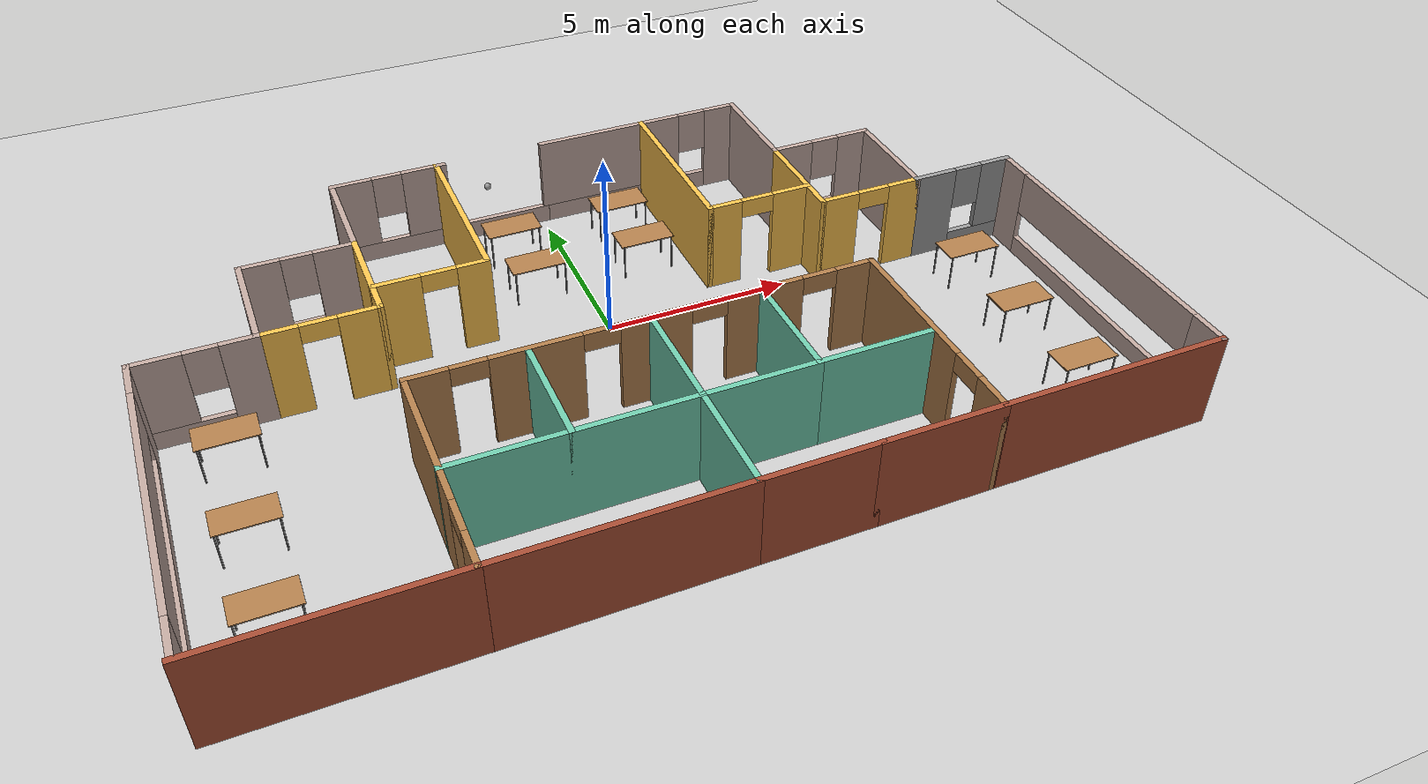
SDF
<sdf version="1.6">
 <world name="default">
  <light name="sun" type="directional">
   <pose>0 0 10 0 -0 0</pose>
   <diffuse>0.8 0.8 0.8 1</diffuse>
   <specular>0.1 0.1 0.1 1</specular>
   <attenuation>
    <range>1000</range>
    <constant>0.9</constant>
    <linear>0.01</linear>
    <quadratic>0.001</quadratic>
   </attenuation>
   <direction>-0.5 0.5 -1</direction>
  </light>
  <model name="ground_plane">
   <static>1</static>
   <link name="link">
    <collision name="collision">
     <geometry><plane><normal>0 0 1</normal><size>100 100</size></plane></geometry>
     <surface><friction><ode><mu>100</mu><mu2>50</mu2></ode></friction></surface>
    </collision>
    <visual name="visual">
     <cast_shadows>0</cast_shadows>
     <geometry><plane><normal>0 0 1</normal><size>100 100</size></plane></geometry>
     <material>
      <script><uri>file://media/materials/scripts/gazebo.material</uri><name>Gazebo/Grey</name></script>
     </material>
    </visual>
   </link>
  </model>
  <gravity>0 0 -9.8</gravity>
  <magnetic_field>6e-06 2.3e-05 -4.2e-05</magnetic_field>
  <atmosphere type="adiabatic"/>
  <physics name="default_physics" default="0" type="ode">
   <max_step_size>0.001</max_step_size>
   <real_time_factor>1</real_time_factor>
   <real_time_update_rate>1000</real_time_update_rate>
  </physics>
  <scene><ambient>0.4 0.4 0.4 1</ambient><background>0.7 0.7 0.7 1</background><shadows>1</shadows></scene>
  <spherical_coordinates>
   <surface_model>EARTH_WGS84</surface_model>
   <latitude_deg>0</latitude_deg>
   <longitude_deg>0</longitude_deg>
   <elevation>0</elevation>
   <heading_deg>0</heading_deg>
  </spherical_coordinates>
  <model name="model">
   <pose>0.101851 -1.62276 0 0 -0 0</pose>
   <link name="Wall_11">
    <pose>2.95 7.2 0 0 -0 3.14159</pose>
    <visual name="Wall_11_Visual_0">
     <pose>-2.50774 0 1.25 0 -0 0</pose>
     <geometry><box><size>0.98451 0.15 2.5</size></box></geometry>
     <material>
      <script><uri>file://media/materials/scripts/gazebo.material</uri><name>Gazebo/Grey</name></script>
      <ambient>0.760784 0.662745 0.627451 1</ambient>
     </material>
     <meta><layer>0</layer></meta>
    </visual>
    <collision name="Wall_11_Collision_0">
     <geometry><box><size>0.98451 0.15 2.5</size></box></geometry>
     <pose>-2.50774 0 1.25 0 -0 0</pose>
    </collision>
    <visual name="Wall_11_Visual_1">
     <pose>0.492255 0 0.25 0 -0 0</pose>
     <geometry><box><size>5.01549 0.15 0.5</size></box></geometry>
     <material>
      <script><uri>file://media/materials/scripts/gazebo.material</uri><name>Gazebo/Grey</name></script>
      <ambient>0.760784 0.662745 0.627451 1</ambient>
     </material>
     <meta><layer>0</layer></meta>
    </visual>
    <collision name="Wall_11_Collision_1">
     <geometry><box><size>5.01549 0.15 0.5</size></box></geometry>
     <pose>0.492255 0 0.25 0 -0 0</pose>
    </collision>
    <visual name="Wall_11_Visual_2">
     <pose>0.892255 0 1.5 0 -0 0</pose>
     <geometry><box><size>4.21549 0.15 2</size></box></geometry>
     <material>
      <script><uri>file://media/materials/scripts/gazebo.material</uri><name>Gazebo/Grey</name></script>
      <ambient>0.760784 0.662745 0.627451 1</ambient>
     </material>
     <meta><layer>0</layer></meta>
    </visual>
    <collision name="Wall_11_Collision_2">
     <geometry><box><size>4.21549 0.15 2</size></box></geometry>
     <pose>0.892255 0 1.5 0 -0 0</pose>
    </collision>
    <visual name="Wall_11_Visual_3">
     <pose>-1.61549 0 1.9 0 -0 0</pose>
     <geometry><box><size>0.8 0.15 1.2</size></box></geometry>
     <material>
      <script><uri>file://media/materials/scripts/gazebo.material</uri><name>Gazebo/Grey</name></script>
      <ambient>0.760784 0.662745 0.627451 1</ambient>
     </material>
     <meta><layer>0</layer></meta>
    </visual>
    <collision name="Wall_11_Collision_3">
     <geometry><box><size>0.8 0.15 1.2</size></box></geometry>
     <pose>-1.61549 0 1.9 0 -0 0</pose>
    </collision>
   </link>
   <link name="Wall_16">
    <collision name="Wall_16_Collision">
     <geometry><box><size>3 0.15 2.5</size></box></geometry>
     <pose>0 0 1.25 0 -0 0</pose>
    </collision>
    <visual name="Wall_16_Visual">
     <pose>0 0 1.25 0 -0 0</pose>
     <geometry><box><size>3 0.15 2.5</size></box></geometry>
     <material>
      <script><uri>file://media/materials/scripts/gazebo.material</uri><name>Gazebo/Grey</name></script>
      <ambient>0.760784 0.662745 0.627451 1</ambient>
     </material>
     <meta><layer>0</layer></meta>
    </visual>
    <pose>5.875 5.775 0 0 -0 -1.5708</pose>
   </link>
   <link name="Wall_17">
    <pose>7.3 4.35 0 0 -0 0</pose>
    <visual name="Wall_17_Visual_0">
     <pose>-0.888143 0 1.25 0 -0 0</pose>
     <geometry><box><size>1.22371 0.15 2.5</size></box></geometry>
     <material>
      <script><uri>file://media/materials/scripts/gazebo.material</uri><name>Gazebo/Grey</name></script>
      <ambient>0.760784 0.662745 0.627451 1</ambient>
     </material>
     <meta><layer>0</layer></meta>
    </visual>
    <collision name="Wall_17_Collision_0">
     <geometry><box><size>1.22371 0.15 2.5</size></box></geometry>
     <pose>-0.888143 0 1.25 0 -0 0</pose>
    </collision>
    <visual name="Wall_17_Visual_1">
     <pose>0.611857 0 0.25 0 -0 0</pose>
     <geometry><box><size>1.77629 0.15 0.5</size></box></geometry>
     <material>
      <script><uri>file://media/materials/scripts/gazebo.material</uri><name>Gazebo/Grey</name></script>
      <ambient>0.760784 0.662745 0.627451 1</ambient>
     </material>
     <meta><layer>0</layer></meta>
    </visual>
    <collision name="Wall_17_Collision_1">
     <geometry><box><size>1.77629 0.15 0.5</size></box></geometry>
     <pose>0.611857 0 0.25 0 -0 0</pose>
    </collision>
    <visual name="Wall_17_Visual_2">
     <pose>1.01186 0 1.5 0 -0 0</pose>
     <geometry><box><size>0.976287 0.15 2</size></box></geometry>
     <material>
      <script><uri>file://media/materials/scripts/gazebo.material</uri><name>Gazebo/Grey</name></script>
      <ambient>0.760784 0.662745 0.627451 1</ambient>
     </material>
     <meta><layer>0</layer></meta>
    </visual>
    <collision name="Wall_17_Collision_2">
     <geometry><box><size>0.976287 0.15 2</size></box></geometry>
     <pose>1.01186 0 1.5 0 -0 0</pose>
    </collision>
    <visual name="Wall_17_Visual_3">
     <pose>0.123713 0 1.9 0 -0 0</pose>
     <geometry><box><size>0.8 0.15 1.2</size></box></geometry>
     <material>
      <script><uri>file://media/materials/scripts/gazebo.material</uri><name>Gazebo/Grey</name></script>
      <ambient>0.760784 0.662745 0.627451 1</ambient>
     </material>
     <meta><layer>0</layer></meta>
    </visual>
    <collision name="Wall_17_Collision_3">
     <geometry><box><size>0.8 0.15 1.2</size></box></geometry>
     <pose>0.123713 0 1.9 0 -0 0</pose>
    </collision>
   </link>
   <link name="Wall_18">
    <collision name="Wall_18_Collision">
     <geometry><box><size>3 0.15 2.5</size></box></geometry>
     <pose>0 0 1.25 0 -0 0</pose>
    </collision>
    <visual name="Wall_18_Visual">
     <pose>0 0 1.25 0 -0 0</pose>
     <geometry><box><size>3 0.15 2.5</size></box></geometry>
     <material>
      <script><uri>file://media/materials/scripts/gazebo.material</uri><name>Gazebo/Grey</name></script>
      <ambient>0.760784 0.662745 0.627451 1</ambient>
     </material>
     <meta><layer>0</layer></meta>
    </visual>
    <pose>8.725 2.925 0 0 -0 -1.5708</pose>
   </link>
   <link name="Wall_19">
    <pose>10.15 1.5 0 0 -0 0</pose>
    <visual name="Wall_19_Visual_0">
     <pose>-0.863411 0 1.25 0 -0 0</pose>
     <geometry><box><size>1.27318 0.15 2.5</size></box></geometry>
     <material>
      <script><uri>file://media/materials/scripts/gazebo.material</uri><name>Gazebo/Grey</name></script>
      <ambient>1 1 1 1</ambient>
     </material>
     <meta><layer>0</layer></meta>
    </visual>
    <collision name="Wall_19_Collision_0">
     <geometry><box><size>1.27318 0.15 2.5</size></box></geometry>
     <pose>-0.863411 0 1.25 0 -0 0</pose>
    </collision>
    <visual name="Wall_19_Visual_1">
     <pose>0.636589 0 0.25 0 -0 0</pose>
     <geometry><box><size>1.72682 0.15 0.5</size></box></geometry>
     <material>
      <script><uri>file://media/materials/scripts/gazebo.material</uri><name>Gazebo/Grey</name></script>
      <ambient>1 1 1 1</ambient>
     </material>
     <meta><layer>0</layer></meta>
    </visual>
    <collision name="Wall_19_Collision_1">
     <geometry><box><size>1.72682 0.15 0.5</size></box></geometry>
     <pose>0.636589 0 0.25 0 -0 0</pose>
    </collision>
    <visual name="Wall_19_Visual_2">
     <pose>1.03659 0 1.5 0 -0 0</pose>
     <geometry><box><size>0.926822 0.15 2</size></box></geometry>
     <material>
      <script><uri>file://media/materials/scripts/gazebo.material</uri><name>Gazebo/Grey</name></script>
      <ambient>1 1 1 1</ambient>
     </material>
     <meta><layer>0</layer></meta>
    </visual>
    <collision name="Wall_19_Collision_2">
     <geometry><box><size>0.926822 0.15 2</size></box></geometry>
     <pose>1.03659 0 1.5 0 -0 0</pose>
    </collision>
    <visual name="Wall_19_Visual_3">
     <pose>0.173178 0 1.9 0 -0 0</pose>
     <geometry><box><size>0.8 0.15 1.2</size></box></geometry>
     <material>
      <script><uri>file://media/materials/scripts/gazebo.material</uri><name>Gazebo/Grey</name></script>
      <ambient>1 1 1 1</ambient>
     </material>
     <meta><layer>0</layer></meta>
    </visual>
    <collision name="Wall_19_Collision_3">
     <geometry><box><size>0.8 0.15 1.2</size></box></geometry>
     <pose>0.173178 0 1.9 0 -0 0</pose>
    </collision>
   </link>
   <link name="Wall_21">
    <collision name="Wall_21_Collision">
     <geometry><box><size>3 0.15 2.5</size></box></geometry>
     <pose>0 0 1.25 0 -0 0</pose>
    </collision>
    <visual name="Wall_21_Visual">
     <pose>0 0 1.25 0 -0 0</pose>
     <geometry><box><size>3 0.15 2.5</size></box></geometry>
     <material>
      <script><uri>file://media/materials/scripts/gazebo.material</uri><name>Gazebo/Grey</name></script>
      <ambient>1 0.764706 0.305882 1</ambient>
     </material>
     <meta><layer>0</layer></meta>
    </visual>
    <pose>5.875 2.925 0 0 -0 -1.5708</pose>
   </link>
   <link name="Wall_22">
    <pose>7.3 1.5 0 0 -0 0</pose>
    <visual name="Wall_22_Visual_0">
     <pose>-0.931281 0 1.25 0 -0 0</pose>
     <geometry><box><size>1.13744 0.15 2.5</size></box></geometry>
     <material>
      <script><uri>file://media/materials/scripts/gazebo.material</uri><name>Gazebo/Grey</name></script>
      <ambient>1 0.764706 0.305882 1</ambient>
     </material>
     <meta><layer>0</layer></meta>
    </visual>
    <collision name="Wall_22_Collision_0">
     <geometry><box><size>1.13744 0.15 2.5</size></box></geometry>
     <pose>-0.931281 0 1.25 0 -0 0</pose>
    </collision>
    <visual name="Wall_22_Visual_1">
     <pose>1.01872 0 1.25 0 -0 0</pose>
     <geometry><box><size>0.962562 0.15 2.5</size></box></geometry>
     <material>
      <script><uri>file://media/materials/scripts/gazebo.material</uri><name>Gazebo/Grey</name></script>
      <ambient>1 0.764706 0.305882 1</ambient>
     </material>
     <meta><layer>0</layer></meta>
    </visual>
    <collision name="Wall_22_Collision_1">
     <geometry><box><size>0.962562 0.15 2.5</size></box></geometry>
     <pose>1.01872 0 1.25 0 -0 0</pose>
    </collision>
    <visual name="Wall_22_Visual_2">
     <pose>0.087438 0 2.25 0 -0 0</pose>
     <geometry><box><size>0.9 0.15 0.5</size></box></geometry>
     <material>
      <script><uri>file://media/materials/scripts/gazebo.material</uri><name>Gazebo/Grey</name></script>
      <ambient>1 0.764706 0.305882 1</ambient>
     </material>
     <meta><layer>0</layer></meta>
    </visual>
    <collision name="Wall_22_Collision_2">
     <geometry><box><size>0.9 0.15 0.5</size></box></geometry>
     <pose>0.087438 0 2.25 0 -0 0</pose>
    </collision>
   </link>
   <link name="Wall_25">
    <collision name="Wall_25_Collision">
     <geometry><box><size>5 0.15 2.5</size></box></geometry>
     <pose>0 0 1.25 0 -0 0</pose>
    </collision>
    <visual name="Wall_25_Visual">
     <pose>0 0 1.25 0 -0 0</pose>
     <geometry><box><size>5 0.15 2.5</size></box></geometry>
     <material>
      <script><uri>file://media/materials/scripts/gazebo.material</uri><name>Gazebo/Grey</name></script>
      <ambient>1 0.764706 0.305882 1</ambient>
     </material>
     <meta><layer>0</layer></meta>
    </visual>
    <pose>3.025 4.775 0 0 -0 -1.5708</pose>
   </link>
   <link name="Wall_26">
    <pose>4.45 2.35 0 0 -0 0</pose>
    <visual name="Wall_26_Visual_0">
     <pose>-1.01278 0 1.25 0 -0 0</pose>
     <geometry><box><size>0.974438 0.15 2.5</size></box></geometry>
     <material>
      <script><uri>file://media/materials/scripts/gazebo.material</uri><name>Gazebo/Grey</name></script>
      <ambient>1 0.764706 0.305882 1</ambient>
     </material>
     <meta><layer>0</layer></meta>
    </visual>
    <collision name="Wall_26_Collision_0">
     <geometry><box><size>0.974438 0.15 2.5</size></box></geometry>
     <pose>-1.01278 0 1.25 0 -0 0</pose>
    </collision>
    <visual name="Wall_26_Visual_1">
     <pose>0.937219 0 1.25 0 -0 0</pose>
     <geometry><box><size>1.12556 0.15 2.5</size></box></geometry>
     <material>
      <script><uri>file://media/materials/scripts/gazebo.material</uri><name>Gazebo/Grey</name></script>
      <ambient>1 0.764706 0.305882 1</ambient>
     </material>
     <meta><layer>0</layer></meta>
    </visual>
    <collision name="Wall_26_Collision_1">
     <geometry><box><size>1.12556 0.15 2.5</size></box></geometry>
     <pose>0.937219 0 1.25 0 -0 0</pose>
    </collision>
    <visual name="Wall_26_Visual_2">
     <pose>-0.075562 0 2.25 0 -0 0</pose>
     <geometry><box><size>0.9 0.15 0.5</size></box></geometry>
     <material>
      <script><uri>file://media/materials/scripts/gazebo.material</uri><name>Gazebo/Grey</name></script>
      <ambient>1 0.764706 0.305882 1</ambient>
     </material>
     <meta><layer>0</layer></meta>
    </visual>
    <collision name="Wall_26_Collision_2">
     <geometry><box><size>0.9 0.15 0.5</size></box></geometry>
     <pose>-0.075562 0 2.25 0 -0 0</pose>
    </collision>
   </link>
   <link name="Wall_32">
    <collision name="Wall_32_Collision">
     <geometry><box><size>6 0.15 2.5</size></box></geometry>
     <pose>0 0 1.25 0 -0 0</pose>
    </collision>
    <visual name="Wall_32_Visual">
     <pose>0 0 1.25 0 -0 0</pose>
     <geometry><box><size>6 0.15 2.5</size></box></geometry>
     <material>
      <script><uri>file://media/materials/scripts/gazebo.material</uri><name>Gazebo/Bricks</name></script>
      <ambient>1 1 1 1</ambient>
     </material>
     <meta><layer>0</layer></meta>
    </visual>
    <pose>8.65 -7.2 0 0 -0 3.14159</pose>
   </link>
   <link name="Wall_34">
    <pose>5.725 -4.275 0 0 -0 1.5708</pose>
    <visual name="Wall_34_Visual_0">
     <pose>-2.46394 0 1.25 0 -0 0</pose>
     <geometry><box><size>1.07212 0.15 2.5</size></box></geometry>
     <material>
      <script><uri>file://media/materials/scripts/gazebo.material</uri><name>Gazebo/Wood</name></script>
      <ambient>1 1 1 1</ambient>
     </material>
     <meta><layer>0</layer></meta>
    </visual>
    <collision name="Wall_34_Collision_0">
     <geometry><box><size>1.07212 0.15 2.5</size></box></geometry>
     <pose>-2.46394 0 1.25 0 -0 0</pose>
    </collision>
    <visual name="Wall_34_Visual_1">
     <pose>0.986061 0 1.25 0 -0 0</pose>
     <geometry><box><size>4.02788 0.15 2.5</size></box></geometry>
     <material>
      <script><uri>file://media/materials/scripts/gazebo.material</uri><name>Gazebo/Wood</name></script>
      <ambient>1 1 1 1</ambient>
     </material>
     <meta><layer>0</layer></meta>
    </visual>
    <collision name="Wall_34_Collision_1">
     <geometry><box><size>4.02788 0.15 2.5</size></box></geometry>
     <pose>0.986061 0 1.25 0 -0 0</pose>
    </collision>
    <visual name="Wall_34_Visual_2">
     <pose>-1.47788 0 2.25 0 -0 0</pose>
     <geometry><box><size>0.9 0.15 0.5</size></box></geometry>
     <material>
      <script><uri>file://media/materials/scripts/gazebo.material</uri><name>Gazebo/Wood</name></script>
      <ambient>1 1 1 1</ambient>
     </material>
     <meta><layer>0</layer></meta>
    </visual>
    <collision name="Wall_34_Collision_2">
     <geometry><box><size>0.9 0.15 0.5</size></box></geometry>
     <pose>-1.47788 0 2.25 0 -0 0</pose>
    </collision>
   </link>
   <link name="Wall_35">
    <pose>2.8 -1.35 0 0 -0 3.14159</pose>
    <visual name="Wall_35_Visual_0">
     <pose>-2.46622 0 1.25 0 -0 0</pose>
     <geometry><box><size>1.06756 0.15 2.5</size></box></geometry>
     <material>
      <script><uri>file://media/materials/scripts/gazebo.material</uri><name>Gazebo/Wood</name></script>
      <ambient>1 1 1 1</ambient>
     </material>
     <meta><layer>0</layer></meta>
    </visual>
    <collision name="Wall_35_Collision_0">
     <geometry><box><size>1.06756 0.15 2.5</size></box></geometry>
     <pose>-2.46622 0 1.25 0 -0 0</pose>
    </collision>
    <visual name="Wall_35_Visual_1">
     <pose>-0.021938 0 1.25 0 -0 0</pose>
     <geometry><box><size>2.021 0.15 2.5</size></box></geometry>
     <material>
      <script><uri>file://media/materials/scripts/gazebo.material</uri><name>Gazebo/Wood</name></script>
      <ambient>1 1 1 1</ambient>
     </material>
     <meta><layer>0</layer></meta>
    </visual>
    <collision name="Wall_35_Collision_1">
     <geometry><box><size>2.021 0.15 2.5</size></box></geometry>
     <pose>-0.021938 0 1.25 0 -0 0</pose>
    </collision>
    <visual name="Wall_35_Visual_2">
     <pose>2.44428 0 1.25 0 -0 0</pose>
     <geometry><box><size>1.11144 0.15 2.5</size></box></geometry>
     <material>
      <script><uri>file://media/materials/scripts/gazebo.material</uri><name>Gazebo/Wood</name></script>
      <ambient>1 1 1 1</ambient>
     </material>
     <meta><layer>0</layer></meta>
    </visual>
    <collision name="Wall_35_Collision_2">
     <geometry><box><size>1.11144 0.15 2.5</size></box></geometry>
     <pose>2.44428 0 1.25 0 -0 0</pose>
    </collision>
    <visual name="Wall_35_Visual_3">
     <pose>-1.48244 0 2.25 0 -0 0</pose>
     <geometry><box><size>0.9 0.15 0.5</size></box></geometry>
     <material>
      <script><uri>file://media/materials/scripts/gazebo.material</uri><name>Gazebo/Wood</name></script>
      <ambient>1 1 1 1</ambient>
     </material>
     <meta><layer>0</layer></meta>
    </visual>
    <collision name="Wall_35_Collision_3">
     <geometry><box><size>0.9 0.15 0.5</size></box></geometry>
     <pose>-1.48244 0 2.25 0 -0 0</pose>
    </collision>
    <visual name="Wall_35_Visual_4">
     <pose>1.43856 0 2.25 0 -0 0</pose>
     <geometry><box><size>0.9 0.15 0.5</size></box></geometry>
     <material>
      <script><uri>file://media/materials/scripts/gazebo.material</uri><name>Gazebo/Wood</name></script>
      <ambient>1 1 1 1</ambient>
     </material>
     <meta><layer>0</layer></meta>
    </visual>
    <collision name="Wall_35_Collision_4">
     <geometry><box><size>0.9 0.15 0.5</size></box></geometry>
     <pose>1.43856 0 2.25 0 -0 0</pose>
    </collision>
   </link>
   <link name="Wall_36">
    <collision name="Wall_36_Collision">
     <geometry><box><size>6 0.15 2.5</size></box></geometry>
     <pose>0 0 1.25 0 -0 0</pose>
    </collision>
    <visual name="Wall_36_Visual">
     <pose>0 0 1.25 0 -0 0</pose>
     <geometry><box><size>6 0.15 2.5</size></box></geometry>
     <material>
      <script><uri>file://media/materials/scripts/gazebo.material</uri><name>Gazebo/Grey</name></script>
      <ambient>0.435294 0.796078 0.67451 1</ambient>
     </material>
     <meta><layer>0</layer></meta>
    </visual>
    <pose>-0.125001 -4.275 0 0 -0 -1.5708</pose>
   </link>
   <link name="Wall_37">
    <collision name="Wall_37_Collision">
     <geometry><box><size>3 0.15 2.5</size></box></geometry>
     <pose>0 0 1.25 0 -0 0</pose>
    </collision>
    <visual name="Wall_37_Visual">
     <pose>0 0 1.25 0 -0 0</pose>
     <geometry><box><size>3 0.15 2.5</size></box></geometry>
     <material>
      <script><uri>file://media/materials/scripts/gazebo.material</uri><name>Gazebo/Bricks</name></script>
      <ambient>1 1 1 1</ambient>
     </material>
     <meta><layer>0</layer></meta>
    </visual>
    <pose>1.3 -7.2 0 0 -0 0</pose>
   </link>
   <link name="Wall_39">
    <collision name="Wall_39_Collision">
     <geometry><box><size>3 0.15 2.5</size></box></geometry>
     <pose>0 0 1.25 0 -0 0</pose>
    </collision>
    <visual name="Wall_39_Visual">
     <pose>0 0 1.25 0 -0 0</pose>
     <geometry><box><size>3 0.15 2.5</size></box></geometry>
     <material>
      <script><uri>file://media/materials/scripts/gazebo.material</uri><name>Gazebo/Grey</name></script>
      <ambient>0.435294 0.796078 0.67451 1</ambient>
     </material>
     <meta><layer>0</layer></meta>
    </visual>
    <pose>1.3 -4.35 0 0 -0 3.14159</pose>
   </link>
   <link name="Wall_41">
    <collision name="Wall_41_Collision">
     <geometry><box><size>3 0.15 2.5</size></box></geometry>
     <pose>0 0 1.25 0 -0 0</pose>
    </collision>
    <visual name="Wall_41_Visual">
     <pose>0 0 1.25 0 -0 0</pose>
     <geometry><box><size>3 0.15 2.5</size></box></geometry>
     <material>
      <script><uri>file://media/materials/scripts/gazebo.material</uri><name>Gazebo/Grey</name></script>
      <ambient>0.435294 0.796078 0.67451 1</ambient>
     </material>
     <meta><layer>0</layer></meta>
    </visual>
    <pose>2.725 -2.925 0 0 -0 1.5708</pose>
   </link>
   <link name="Wall_43">
    <collision name="Wall_43_Collision">
     <geometry><box><size>3 0.15 2.5</size></box></geometry>
     <pose>0 0 1.25 0 -0 0</pose>
    </collision>
    <visual name="Wall_43_Visual">
     <pose>0 0 1.25 0 -0 0</pose>
     <geometry><box><size>3 0.15 2.5</size></box></geometry>
     <material>
      <script><uri>file://media/materials/scripts/gazebo.material</uri><name>Gazebo/Grey</name></script>
      <ambient>0.435294 0.796078 0.67451 1</ambient>
     </material>
     <meta><layer>0</layer></meta>
    </visual>
    <pose>4.15 -4.35 0 0 -0 0</pose>
   </link>
   <link name="Wall_45">
    <collision name="Wall_45_Collision">
     <geometry><box><size>3.15 0.15 2.5</size></box></geometry>
     <pose>0 0 1.25 0 -0 0</pose>
    </collision>
    <visual name="Wall_45_Visual">
     <pose>0 0 1.25 0 -0 0</pose>
     <geometry><box><size>3.15 0.15 2.5</size></box></geometry>
     <material>
      <script><uri>file://media/materials/scripts/gazebo.material</uri><name>Gazebo/Bricks</name></script>
      <ambient>1 1 1 1</ambient>
     </material>
     <meta><layer>0</layer></meta>
    </visual>
    <pose>4.225 -7.2 0 0 -0 0</pose>
   </link>
   <link name="Wall_47">
    <collision name="Wall_47_Collision">
     <geometry><box><size>6 0.15 2.5</size></box></geometry>
     <pose>0 0 1.25 0 -0 0</pose>
    </collision>
    <visual name="Wall_47_Visual">
     <pose>0 0 1.25 0 -0 0</pose>
     <geometry><box><size>6 0.15 2.5</size></box></geometry>
     <material>
      <script><uri>file://media/materials/scripts/gazebo.material</uri><name>Gazebo/Bricks</name></script>
      <ambient>1 1 1 1</ambient>
     </material>
     <meta><layer>0</layer></meta>
    </visual>
    <pose>-3.05 -7.2 0 0 -0 3.14159</pose>
   </link>
   <link name="Wall_48">
    <pose>-5.975 -4.275 0 0 -0 1.5708</pose>
    <visual name="Wall_48_Visual_0">
     <pose>-2.47544 0 1.25 0 -0 0</pose>
     <geometry><box><size>1.04912 0.15 2.5</size></box></geometry>
     <material>
      <script><uri>file://media/materials/scripts/gazebo.material</uri><name>Gazebo/Wood</name></script>
      <ambient>1 1 1 1</ambient>
     </material>
     <meta><layer>0</layer></meta>
    </visual>
    <collision name="Wall_48_Collision_0">
     <geometry><box><size>1.04912 0.15 2.5</size></box></geometry>
     <pose>-2.47544 0 1.25 0 -0 0</pose>
    </collision>
    <visual name="Wall_48_Visual_1">
     <pose>0.974561 0 1.25 0 -0 0</pose>
     <geometry><box><size>4.05088 0.15 2.5</size></box></geometry>
     <material>
      <script><uri>file://media/materials/scripts/gazebo.material</uri><name>Gazebo/Wood</name></script>
      <ambient>1 1 1 1</ambient>
     </material>
     <meta><layer>0</layer></meta>
    </visual>
    <collision name="Wall_48_Collision_1">
     <geometry><box><size>4.05088 0.15 2.5</size></box></geometry>
     <pose>0.974561 0 1.25 0 -0 0</pose>
    </collision>
    <visual name="Wall_48_Visual_2">
     <pose>-1.50088 0 2.25 0 -0 0</pose>
     <geometry><box><size>0.9 0.15 0.5</size></box></geometry>
     <material>
      <script><uri>file://media/materials/scripts/gazebo.material</uri><name>Gazebo/Wood</name></script>
      <ambient>1 1 1 1</ambient>
     </material>
     <meta><layer>0</layer></meta>
    </visual>
    <collision name="Wall_48_Collision_2">
     <geometry><box><size>0.9 0.15 0.5</size></box></geometry>
     <pose>-1.50088 0 2.25 0 -0 0</pose>
    </collision>
   </link>
   <link name="Wall_49">
    <pose>-3.05 -1.35 0 0 -0 0</pose>
    <visual name="Wall_49_Visual_0">
     <pose>-2.45178 0 1.25 0 -0 0</pose>
     <geometry><box><size>1.09644 0.15 2.5</size></box></geometry>
     <material>
      <script><uri>file://media/materials/scripts/gazebo.material</uri><name>Gazebo/Wood</name></script>
      <ambient>1 1 1 1</ambient>
     </material>
     <meta><layer>0</layer></meta>
    </visual>
    <collision name="Wall_49_Collision_0">
     <geometry><box><size>1.09644 0.15 2.5</size></box></geometry>
     <pose>-2.45178 0 1.25 0 -0 0</pose>
    </collision>
    <visual name="Wall_49_Visual_1">
     <pose>0.121938 0 1.25 0 -0 0</pose>
     <geometry><box><size>2.251 0.15 2.5</size></box></geometry>
     <material>
      <script><uri>file://media/materials/scripts/gazebo.material</uri><name>Gazebo/Wood</name></script>
      <ambient>1 1 1 1</ambient>
     </material>
     <meta><layer>0</layer></meta>
    </visual>
    <collision name="Wall_49_Collision_1">
     <geometry><box><size>2.251 0.15 2.5</size></box></geometry>
     <pose>0.121938 0 1.25 0 -0 0</pose>
    </collision>
    <visual name="Wall_49_Visual_2">
     <pose>2.57372 0 1.25 0 -0 0</pose>
     <geometry><box><size>0.852562 0.15 2.5</size></box></geometry>
     <material>
      <script><uri>file://media/materials/scripts/gazebo.material</uri><name>Gazebo/Wood</name></script>
      <ambient>1 1 1 1</ambient>
     </material>
     <meta><layer>0</layer></meta>
    </visual>
    <collision name="Wall_49_Collision_2">
     <geometry><box><size>0.852562 0.15 2.5</size></box></geometry>
     <pose>2.57372 0 1.25 0 -0 0</pose>
    </collision>
    <visual name="Wall_49_Visual_3">
     <pose>-1.45356 0 2.25 0 -0 0</pose>
     <geometry><box><size>0.9 0.15 0.5</size></box></geometry>
     <material>
      <script><uri>file://media/materials/scripts/gazebo.material</uri><name>Gazebo/Wood</name></script>
      <ambient>1 1 1 1</ambient>
     </material>
     <meta><layer>0</layer></meta>
    </visual>
    <collision name="Wall_49_Collision_3">
     <geometry><box><size>0.9 0.15 0.5</size></box></geometry>
     <pose>-1.45356 0 2.25 0 -0 0</pose>
    </collision>
    <visual name="Wall_49_Visual_4">
     <pose>1.69744 0 2.25 0 -0 0</pose>
     <geometry><box><size>0.9 0.15 0.5</size></box></geometry>
     <material>
      <script><uri>file://media/materials/scripts/gazebo.material</uri><name>Gazebo/Wood</name></script>
      <ambient>1 1 1 1</ambient>
     </material>
     <meta><layer>0</layer></meta>
    </visual>
    <collision name="Wall_49_Collision_4">
     <geometry><box><size>0.9 0.15 0.5</size></box></geometry>
     <pose>1.69744 0 2.25 0 -0 0</pose>
    </collision>
   </link>
   <link name="Wall_51">
    <collision name="Wall_51_Collision">
     <geometry><box><size>6 0.15 2.5</size></box></geometry>
     <pose>0 0 1.25 0 -0 0</pose>
    </collision>
    <visual name="Wall_51_Visual">
     <pose>0 0 1.25 0 -0 0</pose>
     <geometry><box><size>6 0.15 2.5</size></box></geometry>
     <material>
      <script><uri>file://media/materials/scripts/gazebo.material</uri><name>Gazebo/Grey</name></script>
      <ambient>0.435294 0.796078 0.67451 1</ambient>
     </material>
     <meta><layer>0</layer></meta>
    </visual>
    <pose>-3.05 -4.35 0 0 -0 3.14159</pose>
   </link>
   <link name="Wall_54">
    <collision name="Wall_54_Collision">
     <geometry><box><size>3 0.15 2.5</size></box></geometry>
     <pose>0 0 1.25 0 -0 0</pose>
    </collision>
    <visual name="Wall_54_Visual">
     <pose>0 0 1.25 0 -0 0</pose>
     <geometry><box><size>3 0.15 2.5</size></box></geometry>
     <material>
      <script><uri>file://media/materials/scripts/gazebo.material</uri><name>Gazebo/Grey</name></script>
      <ambient>0.435294 0.796078 0.67451 1</ambient>
     </material>
     <meta><layer>0</layer></meta>
    </visual>
    <pose>-3.125 -2.925 0 0 -0 1.5708</pose>
   </link>
   <link name="Wall_71">
    <pose>-2.9 7.2 0 0 -0 3.14159</pose>
    <visual name="Wall_71_Visual_0">
     <pose>0 0 0.25 0 -0 0</pose>
     <geometry><box><size>6 0.15 0.5</size></box></geometry>
     <material>
      <script><uri>file://media/materials/scripts/gazebo.material</uri><name>Gazebo/Grey</name></script>
      <ambient>0.760784 0.662745 0.627451 1</ambient>
     </material>
     <meta><layer>0</layer></meta>
    </visual>
    <collision name="Wall_71_Collision_0">
     <geometry><box><size>6 0.15 0.5</size></box></geometry>
     <pose>0 0 0.25 0 -0 0</pose>
    </collision>
    <visual name="Wall_71_Visual_1">
     <pose>0.436212 0 1.5 0 -0 0</pose>
     <geometry><box><size>1.24159 0.15 2</size></box></geometry>
     <material>
      <script><uri>file://media/materials/scripts/gazebo.material</uri><name>Gazebo/Grey</name></script>
      <ambient>0.760784 0.662745 0.627451 1</ambient>
     </material>
     <meta><layer>0</layer></meta>
    </visual>
    <collision name="Wall_71_Collision_1">
     <geometry><box><size>1.24159 0.15 2</size></box></geometry>
     <pose>0.436212 0 1.5 0 -0 0</pose>
    </collision>
    <visual name="Wall_71_Visual_2">
     <pose>2.4285 0 1.5 0 -0 0</pose>
     <geometry><box><size>1.14299 0.15 2</size></box></geometry>
     <material>
      <script><uri>file://media/materials/scripts/gazebo.material</uri><name>Gazebo/Grey</name></script>
      <ambient>0.760784 0.662745 0.627451 1</ambient>
     </material>
     <meta><layer>0</layer></meta>
    </visual>
    <collision name="Wall_71_Collision_2">
     <geometry><box><size>1.14299 0.15 2</size></box></geometry>
     <pose>2.4285 0 1.5 0 -0 0</pose>
    </collision>
    <visual name="Wall_71_Visual_3">
     <pose>1.45701 0 1.9 0 -0 0</pose>
     <geometry><box><size>0.8 0.15 1.2</size></box></geometry>
     <material>
      <script><uri>file://media/materials/scripts/gazebo.material</uri><name>Gazebo/Grey</name></script>
      <ambient>0.760784 0.662745 0.627451 1</ambient>
     </material>
     <meta><layer>0</layer></meta>
    </visual>
    <collision name="Wall_71_Collision_3">
     <geometry><box><size>0.8 0.15 1.2</size></box></geometry>
     <pose>1.45701 0 1.9 0 -0 0</pose>
    </collision>
   </link>
   <link name="Wall_72">
    <collision name="Wall_72_Collision">
     <geometry><box><size>3 0.15 2.5</size></box></geometry>
     <pose>0 0 1.25 0 -0 0</pose>
    </collision>
    <visual name="Wall_72_Visual">
     <pose>0 0 1.25 0 -0 0</pose>
     <geometry><box><size>3 0.15 2.5</size></box></geometry>
     <material>
      <script><uri>file://media/materials/scripts/gazebo.material</uri><name>Gazebo/Grey</name></script>
      <ambient>0.760784 0.662745 0.627451 1</ambient>
     </material>
     <meta><layer>0</layer></meta>
    </visual>
    <pose>-5.825 5.775 0 0 -0 -1.5708</pose>
   </link>
   <link name="Wall_74">
    <pose>-7.25 4.35 0 0 -0 3.14159</pose>
    <visual name="Wall_74_Visual_0">
     <pose>-0.93714 0 1.25 0 -0 0</pose>
     <geometry><box><size>1.12572 0.15 2.5</size></box></geometry>
     <material>
      <script><uri>file://media/materials/scripts/gazebo.material</uri><name>Gazebo/Grey</name></script>
      <ambient>0.760784 0.662745 0.627451 1</ambient>
     </material>
     <meta><layer>0</layer></meta>
    </visual>
    <collision name="Wall_74_Collision_0">
     <geometry><box><size>1.12572 0.15 2.5</size></box></geometry>
     <pose>-0.93714 0 1.25 0 -0 0</pose>
    </collision>
    <visual name="Wall_74_Visual_1">
     <pose>0.56286 0 0.25 0 -0 0</pose>
     <geometry><box><size>1.87428 0.15 0.5</size></box></geometry>
     <material>
      <script><uri>file://media/materials/scripts/gazebo.material</uri><name>Gazebo/Grey</name></script>
      <ambient>0.760784 0.662745 0.627451 1</ambient>
     </material>
     <meta><layer>0</layer></meta>
    </visual>
    <collision name="Wall_74_Collision_1">
     <geometry><box><size>1.87428 0.15 0.5</size></box></geometry>
     <pose>0.56286 0 0.25 0 -0 0</pose>
    </collision>
    <visual name="Wall_74_Visual_2">
     <pose>0.96286 0 1.5 0 -0 0</pose>
     <geometry><box><size>1.07428 0.15 2</size></box></geometry>
     <material>
      <script><uri>file://media/materials/scripts/gazebo.material</uri><name>Gazebo/Grey</name></script>
      <ambient>0.760784 0.662745 0.627451 1</ambient>
     </material>
     <meta><layer>0</layer></meta>
    </visual>
    <collision name="Wall_74_Collision_2">
     <geometry><box><size>1.07428 0.15 2</size></box></geometry>
     <pose>0.96286 0 1.5 0 -0 0</pose>
    </collision>
    <visual name="Wall_74_Visual_3">
     <pose>0.025721 0 1.9 0 -0 0</pose>
     <geometry><box><size>0.8 0.15 1.2</size></box></geometry>
     <material>
      <script><uri>file://media/materials/scripts/gazebo.material</uri><name>Gazebo/Grey</name></script>
      <ambient>0.760784 0.662745 0.627451 1</ambient>
     </material>
     <meta><layer>0</layer></meta>
    </visual>
    <collision name="Wall_74_Collision_3">
     <geometry><box><size>0.8 0.15 1.2</size></box></geometry>
     <pose>0.025721 0 1.9 0 -0 0</pose>
    </collision>
   </link>
   <link name="Wall_75">
    <collision name="Wall_75_Collision">
     <geometry><box><size>3 0.15 2.5</size></box></geometry>
     <pose>0 0 1.25 0 -0 0</pose>
    </collision>
    <visual name="Wall_75_Visual">
     <pose>0 0 1.25 0 -0 0</pose>
     <geometry><box><size>3 0.15 2.5</size></box></geometry>
     <material>
      <script><uri>file://media/materials/scripts/gazebo.material</uri><name>Gazebo/Grey</name></script>
      <ambient>0.760784 0.662745 0.627451 1</ambient>
     </material>
     <meta><layer>0</layer></meta>
    </visual>
    <pose>-8.675 2.925 0 0 -0 -1.5708</pose>
   </link>
   <link name="Wall_77">
    <pose>-10.1 1.5 0 0 -0 3.14159</pose>
    <visual name="Wall_77_Visual_0">
     <pose>-1.03256 0 1.25 0 -0 0</pose>
     <geometry><box><size>0.934877 0.15 2.5</size></box></geometry>
     <material>
      <script><uri>file://media/materials/scripts/gazebo.material</uri><name>Gazebo/Grey</name></script>
      <ambient>0.760784 0.662745 0.627451 1</ambient>
     </material>
     <meta><layer>0</layer></meta>
    </visual>
    <collision name="Wall_77_Collision_0">
     <geometry><box><size>0.934877 0.15 2.5</size></box></geometry>
     <pose>-1.03256 0 1.25 0 -0 0</pose>
    </collision>
    <visual name="Wall_77_Visual_1">
     <pose>0.467439 0 0.25 0 -0 0</pose>
     <geometry><box><size>2.06512 0.15 0.5</size></box></geometry>
     <material>
      <script><uri>file://media/materials/scripts/gazebo.material</uri><name>Gazebo/Grey</name></script>
      <ambient>0.760784 0.662745 0.627451 1</ambient>
     </material>
     <meta><layer>0</layer></meta>
    </visual>
    <collision name="Wall_77_Collision_1">
     <geometry><box><size>2.06512 0.15 0.5</size></box></geometry>
     <pose>0.467439 0 0.25 0 -0 0</pose>
    </collision>
    <visual name="Wall_77_Visual_2">
     <pose>0.867439 0 1.5 0 -0 0</pose>
     <geometry><box><size>1.26512 0.15 2</size></box></geometry>
     <material>
      <script><uri>file://media/materials/scripts/gazebo.material</uri><name>Gazebo/Grey</name></script>
      <ambient>0.760784 0.662745 0.627451 1</ambient>
     </material>
     <meta><layer>0</layer></meta>
    </visual>
    <collision name="Wall_77_Collision_2">
     <geometry><box><size>1.26512 0.15 2</size></box></geometry>
     <pose>0.867439 0 1.5 0 -0 0</pose>
    </collision>
    <visual name="Wall_77_Visual_3">
     <pose>-0.165123 0 1.9 0 -0 0</pose>
     <geometry><box><size>0.8 0.15 1.2</size></box></geometry>
     <material>
      <script><uri>file://media/materials/scripts/gazebo.material</uri><name>Gazebo/Grey</name></script>
      <ambient>0.760784 0.662745 0.627451 1</ambient>
     </material>
     <meta><layer>0</layer></meta>
    </visual>
    <collision name="Wall_77_Collision_3">
     <geometry><box><size>0.8 0.15 1.2</size></box></geometry>
     <pose>-0.165123 0 1.9 0 -0 0</pose>
    </collision>
   </link>
   <link name="Wall_80">
    <pose>-11.525 -2.8 0 0 -0 -1.5708</pose>
    <visual name="Wall_80_Visual_0">
     <pose>-3.84815 0 1.25 0 -0 0</pose>
     <geometry><box><size>1.0537 0.15 2.5</size></box></geometry>
     <material>
      <script><uri>file://media/materials/scripts/gazebo.material</uri><name>Gazebo/Grey</name></script>
      <ambient>0.760784 0.662745 0.627451 1</ambient>
     </material>
     <meta><layer>0</layer></meta>
    </visual>
    <collision name="Wall_80_Collision_0">
     <geometry><box><size>1.0537 0.15 2.5</size></box></geometry>
     <pose>-3.84815 0 1.25 0 -0 0</pose>
    </collision>
    <visual name="Wall_80_Visual_1">
     <pose>0.526847 0 0.25 0 -0 0</pose>
     <geometry><box><size>7.6963 0.15 0.5</size></box></geometry>
     <material>
      <script><uri>file://media/materials/scripts/gazebo.material</uri><name>Gazebo/Grey</name></script>
      <ambient>0.760784 0.662745 0.627451 1</ambient>
     </material>
     <meta><layer>0</layer></meta>
    </visual>
    <collision name="Wall_80_Collision_1">
     <geometry><box><size>7.6963 0.15 0.5</size></box></geometry>
     <pose>0.526847 0 0.25 0 -0 0</pose>
    </collision>
    <visual name="Wall_80_Visual_2">
     <pose>3.85985 0 1.5 0 -0 0</pose>
     <geometry><box><size>1.03031 0.15 2</size></box></geometry>
     <material>
      <script><uri>file://media/materials/scripts/gazebo.material</uri><name>Gazebo/Grey</name></script>
      <ambient>0.760784 0.662745 0.627451 1</ambient>
     </material>
     <meta><layer>0</layer></meta>
    </visual>
    <collision name="Wall_80_Collision_2">
     <geometry><box><size>1.03031 0.15 2</size></box></geometry>
     <pose>3.85985 0 1.5 0 -0 0</pose>
    </collision>
    <visual name="Wall_80_Visual_3">
     <pose>0.011695 0 1.9 0 -0 0</pose>
     <geometry><box><size>6.666 0.15 1.2</size></box></geometry>
     <material>
      <script><uri>file://media/materials/scripts/gazebo.material</uri><name>Gazebo/Grey</name></script>
      <ambient>0.760784 0.662745 0.627451 1</ambient>
     </material>
     <meta><layer>0</layer></meta>
    </visual>
    <collision name="Wall_80_Collision_3">
     <geometry><box><size>6.666 0.15 1.2</size></box></geometry>
     <pose>0.011695 0 1.9 0 -0 0</pose>
    </collision>
   </link>
   <link name="Wall_82">
    <collision name="Wall_82_Collision">
     <geometry><box><size>5.75 0.15 2.5</size></box></geometry>
     <pose>0 0 1.25 0 -0 0</pose>
    </collision>
    <visual name="Wall_82_Visual">
     <pose>0 0 1.25 0 -0 0</pose>
     <geometry><box><size>5.75 0.15 2.5</size></box></geometry>
     <material>
      <script><uri>file://media/materials/scripts/gazebo.material</uri><name>Gazebo/Bricks</name></script>
      <ambient>1 1 1 1</ambient>
     </material>
     <meta><layer>0</layer></meta>
    </visual>
    <pose>-8.775 -7.2 0 0 -0 3.14159</pose>
   </link>
   <link name="Wall_84">
    <pose>-7.25 1.5 0 0 -0 0</pose>
    <visual name="Wall_84_Visual_0">
     <pose>-0.993281 0 1.25 0 -0 0</pose>
     <geometry><box><size>1.01344 0.15 2.5</size></box></geometry>
     <material>
      <script><uri>file://media/materials/scripts/gazebo.material</uri><name>Gazebo/Grey</name></script>
      <ambient>1 0.764706 0.305882 1</ambient>
     </material>
     <meta><layer>0</layer></meta>
    </visual>
    <collision name="Wall_84_Collision_0">
     <geometry><box><size>1.01344 0.15 2.5</size></box></geometry>
     <pose>-0.993281 0 1.25 0 -0 0</pose>
    </collision>
    <visual name="Wall_84_Visual_1">
     <pose>0.956719 0 1.25 0 -0 0</pose>
     <geometry><box><size>1.08656 0.15 2.5</size></box></geometry>
     <material>
      <script><uri>file://media/materials/scripts/gazebo.material</uri><name>Gazebo/Grey</name></script>
      <ambient>1 0.764706 0.305882 1</ambient>
     </material>
     <meta><layer>0</layer></meta>
    </visual>
    <collision name="Wall_84_Collision_1">
     <geometry><box><size>1.08656 0.15 2.5</size></box></geometry>
     <pose>0.956719 0 1.25 0 -0 0</pose>
    </collision>
    <visual name="Wall_84_Visual_2">
     <pose>-0.036562 0 2.25 0 -0 0</pose>
     <geometry><box><size>0.9 0.15 0.5</size></box></geometry>
     <material>
      <script><uri>file://media/materials/scripts/gazebo.material</uri><name>Gazebo/Grey</name></script>
      <ambient>1 0.764706 0.305882 1</ambient>
     </material>
     <meta><layer>0</layer></meta>
    </visual>
    <collision name="Wall_84_Collision_2">
     <geometry><box><size>0.9 0.15 0.5</size></box></geometry>
     <pose>-0.036562 0 2.25 0 -0 0</pose>
    </collision>
   </link>
   <link name="Wall_85">
    <collision name="Wall_85_Collision">
     <geometry><box><size>3 0.15 2.5</size></box></geometry>
     <pose>0 0 1.25 0 -0 0</pose>
    </collision>
    <visual name="Wall_85_Visual">
     <pose>0 0 1.25 0 -0 0</pose>
     <geometry><box><size>3 0.15 2.5</size></box></geometry>
     <material>
      <script><uri>file://media/materials/scripts/gazebo.material</uri><name>Gazebo/Grey</name></script>
      <ambient>1 0.764706 0.305882 1</ambient>
     </material>
     <meta><layer>0</layer></meta>
    </visual>
    <pose>-5.825 2.925 0 0 -0 1.5708</pose>
   </link>
   <link name="Wall_88">
    <collision name="Wall_88_Collision">
     <geometry><box><size>5 0.15 2.5</size></box></geometry>
     <pose>0 0 1.25 0 -0 0</pose>
    </collision>
    <visual name="Wall_88_Visual">
     <pose>0 0 1.25 0 -0 0</pose>
     <geometry><box><size>5 0.15 2.5</size></box></geometry>
     <material>
      <script><uri>file://media/materials/scripts/gazebo.material</uri><name>Gazebo/Grey</name></script>
      <ambient>1 0.764706 0.305882 1</ambient>
     </material>
     <meta><layer>0</layer></meta>
    </visual>
    <pose>-2.975 4.775 0 0 -0 -1.5708</pose>
   </link>
   <link name="Wall_89">
    <pose>-4.4 2.35 0 0 -0 3.14159</pose>
    <visual name="Wall_89_Visual_0">
     <pose>-1.07272 0 1.25 0 -0 0</pose>
     <geometry><box><size>0.854562 0.15 2.5</size></box></geometry>
     <material>
      <script><uri>file://media/materials/scripts/gazebo.material</uri><name>Gazebo/Grey</name></script>
      <ambient>1 0.764706 0.305882 1</ambient>
     </material>
     <meta><layer>0</layer></meta>
    </visual>
    <collision name="Wall_89_Collision_0">
     <geometry><box><size>0.854562 0.15 2.5</size></box></geometry>
     <pose>-1.07272 0 1.25 0 -0 0</pose>
    </collision>
    <visual name="Wall_89_Visual_1">
     <pose>0.877281 0 1.25 0 -0 0</pose>
     <geometry><box><size>1.24544 0.15 2.5</size></box></geometry>
     <material>
      <script><uri>file://media/materials/scripts/gazebo.material</uri><name>Gazebo/Grey</name></script>
      <ambient>1 0.764706 0.305882 1</ambient>
     </material>
     <meta><layer>0</layer></meta>
    </visual>
    <collision name="Wall_89_Collision_1">
     <geometry><box><size>1.24544 0.15 2.5</size></box></geometry>
     <pose>0.877281 0 1.25 0 -0 0</pose>
    </collision>
    <visual name="Wall_89_Visual_2">
     <pose>-0.195438 0 2.25 0 -0 0</pose>
     <geometry><box><size>0.9 0.15 0.5</size></box></geometry>
     <material>
      <script><uri>file://media/materials/scripts/gazebo.material</uri><name>Gazebo/Grey</name></script>
      <ambient>1 0.764706 0.305882 1</ambient>
     </material>
     <meta><layer>0</layer></meta>
    </visual>
    <collision name="Wall_89_Collision_2">
     <geometry><box><size>0.9 0.15 0.5</size></box></geometry>
     <pose>-0.195438 0 2.25 0 -0 0</pose>
    </collision>
   </link>
   <link name="Wall_91">
    <pose>11.575 -2.85 0 0 -0 -1.5708</pose>
    <visual name="Wall_91_Visual_0">
     <pose>-3.90506 0 1.25 0 -0 0</pose>
     <geometry><box><size>1.03988 0.15 2.5</size></box></geometry>
     <material>
      <script><uri>file://media/materials/scripts/gazebo.material</uri><name>Gazebo/Grey</name></script>
      <ambient>0.760784 0.662745 0.627451 1</ambient>
     </material>
     <meta><layer>0</layer></meta>
    </visual>
    <collision name="Wall_91_Collision_0">
     <geometry><box><size>1.03988 0.15 2.5</size></box></geometry>
     <pose>-3.90506 0 1.25 0 -0 0</pose>
    </collision>
    <visual name="Wall_91_Visual_1">
     <pose>0.519939 0 0.25 0 -0 0</pose>
     <geometry><box><size>7.81012 0.15 0.5</size></box></geometry>
     <material>
      <script><uri>file://media/materials/scripts/gazebo.material</uri><name>Gazebo/Grey</name></script>
      <ambient>0.760784 0.662745 0.627451 1</ambient>
     </material>
     <meta><layer>0</layer></meta>
    </visual>
    <collision name="Wall_91_Collision_1">
     <geometry><box><size>7.81012 0.15 0.5</size></box></geometry>
     <pose>0.519939 0 0.25 0 -0 0</pose>
    </collision>
    <visual name="Wall_91_Visual_2">
     <pose>3.90994 0 1.5 0 -0 0</pose>
     <geometry><box><size>1.03012 0.15 2</size></box></geometry>
     <material>
      <script><uri>file://media/materials/scripts/gazebo.material</uri><name>Gazebo/Grey</name></script>
      <ambient>0.760784 0.662745 0.627451 1</ambient>
     </material>
     <meta><layer>0</layer></meta>
    </visual>
    <collision name="Wall_91_Collision_2">
     <geometry><box><size>1.03012 0.15 2</size></box></geometry>
     <pose>3.90994 0 1.5 0 -0 0</pose>
    </collision>
    <visual name="Wall_91_Visual_3">
     <pose>0.004877 0 1.9 0 -0 0</pose>
     <geometry><box><size>6.78 0.15 1.2</size></box></geometry>
     <material>
      <script><uri>file://media/materials/scripts/gazebo.material</uri><name>Gazebo/Grey</name></script>
      <ambient>0.760784 0.662745 0.627451 1</ambient>
     </material>
     <meta><layer>0</layer></meta>
    </visual>
    <collision name="Wall_91_Collision_3">
     <geometry><box><size>6.78 0.15 1.2</size></box></geometry>
     <pose>0.004877 0 1.9 0 -0 0</pose>
    </collision>
   </link>
   <static>1</static>
  </model>
  <model name="table">
   <static>1</static>
   <link name="link">
    <collision name="surface">
     <pose>0 0 1 0 -0 0</pose>
     <geometry><box><size>1.5 0.8 0.03</size></box></geometry>
     <surface><friction><ode><mu>0.6</mu><mu2>0.6</mu2></ode></friction></surface>
    </collision>
    <visual name="visual1">
     <pose>0 0 1 0 -0 0</pose>
     <geometry><box><size>1.5 0.8 0.03</size></box></geometry>
     <material>
      <script><uri>file://media/materials/scripts/gazebo.material</uri><name>Gazebo/Wood</name></script>
     </material>
    </visual>
    <collision name="front_left_leg">
     <pose>0.68 0.38 0.5 0 -0 0</pose>
     <geometry><cylinder><radius>0.02</radius><length>1</length></cylinder></geometry>
    </collision>
    <visual name="front_left_leg">
     <pose>0.68 0.38 0.5 0 -0 0</pose>
     <geometry><cylinder><radius>0.02</radius><length>1</length></cylinder></geometry>
     <material>
      <script><uri>file://media/materials/scripts/gazebo.material</uri><name>Gazebo/Grey</name></script>
     </material>
    </visual>
    <collision name="front_right_leg">
     <pose>0.68 -0.38 0.5 0 -0 0</pose>
     <geometry><cylinder><radius>0.02</radius><length>1</length></cylinder></geometry>
    </collision>
    <visual name="front_right_leg">
     <pose>0.68 -0.38 0.5 0 -0 0</pose>
     <geometry><cylinder><radius>0.02</radius><length>1</length></cylinder></geometry>
     <material>
      <script><uri>file://media/materials/scripts/gazebo.material</uri><name>Gazebo/Grey</name></script>
     </material>
    </visual>
    <collision name="back_right_leg">
     <pose>-0.68 -0.38 0.5 0 -0 0</pose>
     <geometry><cylinder><radius>0.02</radius><length>1</length></cylinder></geometry>
    </collision>
    <visual name="back_right_leg">
     <pose>-0.68 -0.38 0.5 0 -0 0</pose>
     <geometry><cylinder><radius>0.02</radius><length>1</length></cylinder></geometry>
     <material>
      <script><uri>file://media/materials/scripts/gazebo.material</uri><name>Gazebo/Grey</name></script>
     </material>
    </visual>
    <collision name="back_left_leg">
     <pose>-0.68 0.38 0.5 0 -0 0</pose>
     <geometry><cylinder><radius>0.02</radius><length>1</length></cylinder></geometry>
    </collision>
    <visual name="back_left_leg">
     <pose>-0.68 0.38 0.5 0 -0 0</pose>
     <geometry><cylinder><radius>0.02</radius><length>1</length></cylinder></geometry>
     <material>
      <script><uri>file://media/materials/scripts/gazebo.material</uri><name>Gazebo/Grey</name></script>
     </material>
    </visual>
   </link>
   <pose>1.85781 4.2341 0 0 -0 0</pose>
  </model>
  <model name="table_clone">
   <static>1</static>
   <link name="link">
    <collision name="surface">
     <pose>0 0 1 0 -0 0</pose>
     <geometry><box><size>1.5 0.8 0.03</size></box></geometry>
     <surface><friction><ode><mu>0.6</mu><mu2>0.6</mu2></ode></friction></surface>
    </collision>
    <visual name="visual1">
     <pose>0 0 1 0 -0 0</pose>
     <geometry><box><size>1.5 0.8 0.03</size></box></geometry>
     <material>
      <script><uri>file://media/materials/scripts/gazebo.material</uri><name>Gazebo/Wood</name></script>
     </material>
    </visual>
    <collision name="front_left_leg">
     <pose>0.68 0.38 0.5 0 -0 0</pose>
     <geometry><cylinder><radius>0.02</radius><length>1</length></cylinder></geometry>
    </collision>
    <visual name="front_left_leg">
     <pose>0.68 0.38 0.5 0 -0 0</pose>
     <geometry><cylinder><radius>0.02</radius><length>1</length></cylinder></geometry>
     <material>
      <script><uri>file://media/materials/scripts/gazebo.material</uri><name>Gazebo/Grey</name></script>
     </material>
    </visual>
    <collision name="front_right_leg">
     <pose>0.68 -0.38 0.5 0 -0 0</pose>
     <geometry><cylinder><radius>0.02</radius><length>1</length></cylinder></geometry>
    </collision>
    <visual name="front_right_leg">
     <pose>0.68 -0.38 0.5 0 -0 0</pose>
     <geometry><cylinder><radius>0.02</radius><length>1</length></cylinder></geometry>
     <material>
      <script><uri>file://media/materials/scripts/gazebo.material</uri><name>Gazebo/Grey</name></script>
     </material>
    </visual>
    <collision name="back_right_leg">
     <pose>-0.68 -0.38 0.5 0 -0 0</pose>
     <geometry><cylinder><radius>0.02</radius><length>1</length></cylinder></geometry>
    </collision>
    <visual name="back_right_leg">
     <pose>-0.68 -0.38 0.5 0 -0 0</pose>
     <geometry><cylinder><radius>0.02</radius><length>1</length></cylinder></geometry>
     <material>
      <script><uri>file://media/materials/scripts/gazebo.material</uri><name>Gazebo/Grey</name></script>
     </material>
    </visual>
    <collision name="back_left_leg">
     <pose>-0.68 0.38 0.5 0 -0 0</pose>
     <geometry><cylinder><radius>0.02</radius><length>1</length></cylinder></geometry>
    </collision>
    <visual name="back_left_leg">
     <pose>-0.68 0.38 0.5 0 -0 0</pose>
     <geometry><cylinder><radius>0.02</radius><length>1</length></cylinder></geometry>
     <material>
      <script><uri>file://media/materials/scripts/gazebo.material</uri><name>Gazebo/Grey</name></script>
     </material>
    </visual>
   </link>
   <pose>1.85781 2.33238 0 0 -0 0</pose>
  </model>
  <model name="table_clone_0">
   <static>1</static>
   <link name="link">
    <collision name="surface">
     <pose>0 0 1 0 -0 0</pose>
     <geometry><box><size>1.5 0.8 0.03</size></box></geometry>
     <surface><friction><ode><mu>0.6</mu><mu2>0.6</mu2></ode></friction></surface>
    </collision>
    <visual name="visual1">
     <pose>0 0 1 0 -0 0</pose>
     <geometry><box><size>1.5 0.8 0.03</size></box></geometry>
     <material>
      <script><uri>file://media/materials/scripts/gazebo.material</uri><name>Gazebo/Wood</name></script>
     </material>
    </visual>
    <collision name="front_left_leg">
     <pose>0.68 0.38 0.5 0 -0 0</pose>
     <geometry><cylinder><radius>0.02</radius><length>1</length></cylinder></geometry>
    </collision>
    <visual name="front_left_leg">
     <pose>0.68 0.38 0.5 0 -0 0</pose>
     <geometry><cylinder><radius>0.02</radius><length>1</length></cylinder></geometry>
     <material>
      <script><uri>file://media/materials/scripts/gazebo.material</uri><name>Gazebo/Grey</name></script>
     </material>
    </visual>
    <collision name="front_right_leg">
     <pose>0.68 -0.38 0.5 0 -0 0</pose>
     <geometry><cylinder><radius>0.02</radius><length>1</length></cylinder></geometry>
    </collision>
    <visual name="front_right_leg">
     <pose>0.68 -0.38 0.5 0 -0 0</pose>
     <geometry><cylinder><radius>0.02</radius><length>1</length></cylinder></geometry>
     <material>
      <script><uri>file://media/materials/scripts/gazebo.material</uri><name>Gazebo/Grey</name></script>
     </material>
    </visual>
    <collision name="back_right_leg">
     <pose>-0.68 -0.38 0.5 0 -0 0</pose>
     <geometry><cylinder><radius>0.02</radius><length>1</length></cylinder></geometry>
    </collision>
    <visual name="back_right_leg">
     <pose>-0.68 -0.38 0.5 0 -0 0</pose>
     <geometry><cylinder><radius>0.02</radius><length>1</length></cylinder></geometry>
     <material>
      <script><uri>file://media/materials/scripts/gazebo.material</uri><name>Gazebo/Grey</name></script>
     </material>
    </visual>
    <collision name="back_left_leg">
     <pose>-0.68 0.38 0.5 0 -0 0</pose>
     <geometry><cylinder><radius>0.02</radius><length>1</length></cylinder></geometry>
    </collision>
    <visual name="back_left_leg">
     <pose>-0.68 0.38 0.5 0 -0 0</pose>
     <geometry><cylinder><radius>0.02</radius><length>1</length></cylinder></geometry>
     <material>
      <script><uri>file://media/materials/scripts/gazebo.material</uri><name>Gazebo/Grey</name></script>
     </material>
    </visual>
   </link>
   <pose>-1.31169 4.15802 0 0 -0 0</pose>
  </model>
  <model name="table_clone_1">
   <static>1</static>
   <link name="link">
    <collision name="surface">
     <pose>0 0 1 0 -0 0</pose>
     <geometry><box><size>1.5 0.8 0.03</size></box></geometry>
     <surface><friction><ode><mu>0.6</mu><mu2>0.6</mu2></ode></friction></surface>
    </collision>
    <visual name="visual1">
     <pose>0 0 1 0 -0 0</pose>
     <geometry><box><size>1.5 0.8 0.03</size></box></geometry>
     <material>
      <script><uri>file://media/materials/scripts/gazebo.material</uri><name>Gazebo/Wood</name></script>
     </material>
    </visual>
    <collision name="front_left_leg">
     <pose>0.68 0.38 0.5 0 -0 0</pose>
     <geometry><cylinder><radius>0.02</radius><length>1</length></cylinder></geometry>
    </collision>
    <visual name="front_left_leg">
     <pose>0.68 0.38 0.5 0 -0 0</pose>
     <geometry><cylinder><radius>0.02</radius><length>1</length></cylinder></geometry>
     <material>
      <script><uri>file://media/materials/scripts/gazebo.material</uri><name>Gazebo/Grey</name></script>
     </material>
    </visual>
    <collision name="front_right_leg">
     <pose>0.68 -0.38 0.5 0 -0 0</pose>
     <geometry><cylinder><radius>0.02</radius><length>1</length></cylinder></geometry>
    </collision>
    <visual name="front_right_leg">
     <pose>0.68 -0.38 0.5 0 -0 0</pose>
     <geometry><cylinder><radius>0.02</radius><length>1</length></cylinder></geometry>
     <material>
      <script><uri>file://media/materials/scripts/gazebo.material</uri><name>Gazebo/Grey</name></script>
     </material>
    </visual>
    <collision name="back_right_leg">
     <pose>-0.68 -0.38 0.5 0 -0 0</pose>
     <geometry><cylinder><radius>0.02</radius><length>1</length></cylinder></geometry>
    </collision>
    <visual name="back_right_leg">
     <pose>-0.68 -0.38 0.5 0 -0 0</pose>
     <geometry><cylinder><radius>0.02</radius><length>1</length></cylinder></geometry>
     <material>
      <script><uri>file://media/materials/scripts/gazebo.material</uri><name>Gazebo/Grey</name></script>
     </material>
    </visual>
    <collision name="back_left_leg">
     <pose>-0.68 0.38 0.5 0 -0 0</pose>
     <geometry><cylinder><radius>0.02</radius><length>1</length></cylinder></geometry>
    </collision>
    <visual name="back_left_leg">
     <pose>-0.68 0.38 0.5 0 -0 0</pose>
     <geometry><cylinder><radius>0.02</radius><length>1</length></cylinder></geometry>
     <material>
      <script><uri>file://media/materials/scripts/gazebo.material</uri><name>Gazebo/Grey</name></script>
     </material>
    </visual>
   </link>
   <pose>-1.21027 2.28167 0 0 -0 0</pose>
  </model>
  <model name="table_clone_2">
   <static>1</static>
   <link name="link">
    <collision name="surface">
     <pose>0 0 1 0 -0 0</pose>
     <geometry><box><size>1.5 0.8 0.03</size></box></geometry>
     <surface><friction><ode><mu>0.6</mu><mu2>0.6</mu2></ode></friction></surface>
    </collision>
    <visual name="visual1">
     <pose>0 0 1 0 -0 0</pose>
     <geometry><box><size>1.5 0.8 0.03</size></box></geometry>
     <material>
      <script><uri>file://media/materials/scripts/gazebo.material</uri><name>Gazebo/Wood</name></script>
     </material>
    </visual>
    <collision name="front_left_leg">
     <pose>0.68 0.38 0.5 0 -0 0</pose>
     <geometry><cylinder><radius>0.02</radius><length>1</length></cylinder></geometry>
    </collision>
    <visual name="front_left_leg">
     <pose>0.68 0.38 0.5 0 -0 0</pose>
     <geometry><cylinder><radius>0.02</radius><length>1</length></cylinder></geometry>
     <material>
      <script><uri>file://media/materials/scripts/gazebo.material</uri><name>Gazebo/Grey</name></script>
     </material>
    </visual>
    <collision name="front_right_leg">
     <pose>0.68 -0.38 0.5 0 -0 0</pose>
     <geometry><cylinder><radius>0.02</radius><length>1</length></cylinder></geometry>
    </collision>
    <visual name="front_right_leg">
     <pose>0.68 -0.38 0.5 0 -0 0</pose>
     <geometry><cylinder><radius>0.02</radius><length>1</length></cylinder></geometry>
     <material>
      <script><uri>file://media/materials/scripts/gazebo.material</uri><name>Gazebo/Grey</name></script>
     </material>
    </visual>
    <collision name="back_right_leg">
     <pose>-0.68 -0.38 0.5 0 -0 0</pose>
     <geometry><cylinder><radius>0.02</radius><length>1</length></cylinder></geometry>
    </collision>
    <visual name="back_right_leg">
     <pose>-0.68 -0.38 0.5 0 -0 0</pose>
     <geometry><cylinder><radius>0.02</radius><length>1</length></cylinder></geometry>
     <material>
      <script><uri>file://media/materials/scripts/gazebo.material</uri><name>Gazebo/Grey</name></script>
     </material>
    </visual>
    <collision name="back_left_leg">
     <pose>-0.68 0.38 0.5 0 -0 0</pose>
     <geometry><cylinder><radius>0.02</radius><length>1</length></cylinder></geometry>
    </collision>
    <visual name="back_left_leg">
     <pose>-0.68 0.38 0.5 0 -0 0</pose>
     <geometry><cylinder><radius>0.02</radius><length>1</length></cylinder></geometry>
     <material>
      <script><uri>file://media/materials/scripts/gazebo.material</uri><name>Gazebo/Grey</name></script>
     </material>
    </visual>
   </link>
   <pose>9.73733 -1.53615 0 0 -0 0</pose>
  </model>
  <model name="table_clone_3">
   <static>1</static>
   <link name="link">
    <collision name="surface">
     <pose>0 0 1 0 -0 0</pose>
     <geometry><box><size>1.5 0.8 0.03</size></box></geometry>
     <surface><friction><ode><mu>0.6</mu><mu2>0.6</mu2></ode></friction></surface>
    </collision>
    <visual name="visual1">
     <pose>0 0 1 0 -0 0</pose>
     <geometry><box><size>1.5 0.8 0.03</size></box></geometry>
     <material>
      <script><uri>file://media/materials/scripts/gazebo.material</uri><name>Gazebo/Wood</name></script>
     </material>
    </visual>
    <collision name="front_left_leg">
     <pose>0.68 0.38 0.5 0 -0 0</pose>
     <geometry><cylinder><radius>0.02</radius><length>1</length></cylinder></geometry>
    </collision>
    <visual name="front_left_leg">
     <pose>0.68 0.38 0.5 0 -0 0</pose>
     <geometry><cylinder><radius>0.02</radius><length>1</length></cylinder></geometry>
     <material>
      <script><uri>file://media/materials/scripts/gazebo.material</uri><name>Gazebo/Grey</name></script>
     </material>
    </visual>
    <collision name="front_right_leg">
     <pose>0.68 -0.38 0.5 0 -0 0</pose>
     <geometry><cylinder><radius>0.02</radius><length>1</length></cylinder></geometry>
    </collision>
    <visual name="front_right_leg">
     <pose>0.68 -0.38 0.5 0 -0 0</pose>
     <geometry><cylinder><radius>0.02</radius><length>1</length></cylinder></geometry>
     <material>
      <script><uri>file://media/materials/scripts/gazebo.material</uri><name>Gazebo/Grey</name></script>
     </material>
    </visual>
    <collision name="back_right_leg">
     <pose>-0.68 -0.38 0.5 0 -0 0</pose>
     <geometry><cylinder><radius>0.02</radius><length>1</length></cylinder></geometry>
    </collision>
    <visual name="back_right_leg">
     <pose>-0.68 -0.38 0.5 0 -0 0</pose>
     <geometry><cylinder><radius>0.02</radius><length>1</length></cylinder></geometry>
     <material>
      <script><uri>file://media/materials/scripts/gazebo.material</uri><name>Gazebo/Grey</name></script>
     </material>
    </visual>
    <collision name="back_left_leg">
     <pose>-0.68 0.38 0.5 0 -0 0</pose>
     <geometry><cylinder><radius>0.02</radius><length>1</length></cylinder></geometry>
    </collision>
    <visual name="back_left_leg">
     <pose>-0.68 0.38 0.5 0 -0 0</pose>
     <geometry><cylinder><radius>0.02</radius><length>1</length></cylinder></geometry>
     <material>
      <script><uri>file://media/materials/scripts/gazebo.material</uri><name>Gazebo/Grey</name></script>
     </material>
    </visual>
   </link>
   <pose>9.70496 -4.0717 0 0 -0 0</pose>
  </model>
  <model name="table_clone_4">
   <static>1</static>
   <link name="link">
    <collision name="surface">
     <pose>0 0 1 0 -0 0</pose>
     <geometry><box><size>1.5 0.8 0.03</size></box></geometry>
     <surface><friction><ode><mu>0.6</mu><mu2>0.6</mu2></ode></friction></surface>
    </collision>
    <visual name="visual1">
     <pose>0 0 1 0 -0 0</pose>
     <geometry><box><size>1.5 0.8 0.03</size></box></geometry>
     <material>
      <script><uri>file://media/materials/scripts/gazebo.material</uri><name>Gazebo/Wood</name></script>
     </material>
    </visual>
    <collision name="front_left_leg">
     <pose>0.68 0.38 0.5 0 -0 0</pose>
     <geometry><cylinder><radius>0.02</radius><length>1</length></cylinder></geometry>
    </collision>
    <visual name="front_left_leg">
     <pose>0.68 0.38 0.5 0 -0 0</pose>
     <geometry><cylinder><radius>0.02</radius><length>1</length></cylinder></geometry>
     <material>
      <script><uri>file://media/materials/scripts/gazebo.material</uri><name>Gazebo/Grey</name></script>
     </material>
    </visual>
    <collision name="front_right_leg">
     <pose>0.68 -0.38 0.5 0 -0 0</pose>
     <geometry><cylinder><radius>0.02</radius><length>1</length></cylinder></geometry>
    </collision>
    <visual name="front_right_leg">
     <pose>0.68 -0.38 0.5 0 -0 0</pose>
     <geometry><cylinder><radius>0.02</radius><length>1</length></cylinder></geometry>
     <material>
      <script><uri>file://media/materials/scripts/gazebo.material</uri><name>Gazebo/Grey</name></script>
     </material>
    </visual>
    <collision name="back_right_leg">
     <pose>-0.68 -0.38 0.5 0 -0 0</pose>
     <geometry><cylinder><radius>0.02</radius><length>1</length></cylinder></geometry>
    </collision>
    <visual name="back_right_leg">
     <pose>-0.68 -0.38 0.5 0 -0 0</pose>
     <geometry><cylinder><radius>0.02</radius><length>1</length></cylinder></geometry>
     <material>
      <script><uri>file://media/materials/scripts/gazebo.material</uri><name>Gazebo/Grey</name></script>
     </material>
    </visual>
    <collision name="back_left_leg">
     <pose>-0.68 0.38 0.5 0 -0 0</pose>
     <geometry><cylinder><radius>0.02</radius><length>1</length></cylinder></geometry>
    </collision>
    <visual name="back_left_leg">
     <pose>-0.68 0.38 0.5 0 -0 0</pose>
     <geometry><cylinder><radius>0.02</radius><length>1</length></cylinder></geometry>
     <material>
      <script><uri>file://media/materials/scripts/gazebo.material</uri><name>Gazebo/Grey</name></script>
     </material>
    </visual>
   </link>
   <pose>9.75569 -6.63275 0 0 -0 0</pose>
  </model>
  <model name="table_clone_5">
   <static>1</static>
   <link name="link">
    <collision name="surface">
     <pose>0 0 1 0 -0 0</pose>
     <geometry><box><size>1.5 0.8 0.03</size></box></geometry>
     <surface><friction><ode><mu>0.6</mu><mu2>0.6</mu2></ode></friction></surface>
    </collision>
    <visual name="visual1">
     <pose>0 0 1 0 -0 0</pose>
     <geometry><box><size>1.5 0.8 0.03</size></box></geometry>
     <material>
      <script><uri>file://media/materials/scripts/gazebo.material</uri><name>Gazebo/Wood</name></script>
     </material>
    </visual>
    <collision name="front_left_leg">
     <pose>0.68 0.38 0.5 0 -0 0</pose>
     <geometry><cylinder><radius>0.02</radius><length>1</length></cylinder></geometry>
    </collision>
    <visual name="front_left_leg">
     <pose>0.68 0.38 0.5 0 -0 0</pose>
     <geometry><cylinder><radius>0.02</radius><length>1</length></cylinder></geometry>
     <material>
      <script><uri>file://media/materials/scripts/gazebo.material</uri><name>Gazebo/Grey</name></script>
     </material>
    </visual>
    <collision name="front_right_leg">
     <pose>0.68 -0.38 0.5 0 -0 0</pose>
     <geometry><cylinder><radius>0.02</radius><length>1</length></cylinder></geometry>
    </collision>
    <visual name="front_right_leg">
     <pose>0.68 -0.38 0.5 0 -0 0</pose>
     <geometry><cylinder><radius>0.02</radius><length>1</length></cylinder></geometry>
     <material>
      <script><uri>file://media/materials/scripts/gazebo.material</uri><name>Gazebo/Grey</name></script>
     </material>
    </visual>
    <collision name="back_right_leg">
     <pose>-0.68 -0.38 0.5 0 -0 0</pose>
     <geometry><cylinder><radius>0.02</radius><length>1</length></cylinder></geometry>
    </collision>
    <visual name="back_right_leg">
     <pose>-0.68 -0.38 0.5 0 -0 0</pose>
     <geometry><cylinder><radius>0.02</radius><length>1</length></cylinder></geometry>
     <material>
      <script><uri>file://media/materials/scripts/gazebo.material</uri><name>Gazebo/Grey</name></script>
     </material>
    </visual>
    <collision name="back_left_leg">
     <pose>-0.68 0.38 0.5 0 -0 0</pose>
     <geometry><cylinder><radius>0.02</radius><length>1</length></cylinder></geometry>
    </collision>
    <visual name="back_left_leg">
     <pose>-0.68 0.38 0.5 0 -0 0</pose>
     <geometry><cylinder><radius>0.02</radius><length>1</length></cylinder></geometry>
     <material>
      <script><uri>file://media/materials/scripts/gazebo.material</uri><name>Gazebo/Grey</name></script>
     </material>
    </visual>
   </link>
   <pose>-9.75691 -1.38623 0 0 -0 0</pose>
  </model>
  <model name="table_clone_6">
   <static>1</static>
   <link name="link">
    <collision name="surface">
     <pose>0 0 1 0 -0 0</pose>
     <geometry><box><size>1.5 0.8 0.03</size></box></geometry>
     <surface><friction><ode><mu>0.6</mu><mu2>0.6</mu2></ode></friction></surface>
    </collision>
    <visual name="visual1">
     <pose>0 0 1 0 -0 0</pose>
     <geometry><box><size>1.5 0.8 0.03</size></box></geometry>
     <material>
      <script><uri>file://media/materials/scripts/gazebo.material</uri><name>Gazebo/Wood</name></script>
     </material>
    </visual>
    <collision name="front_left_leg">
     <pose>0.68 0.38 0.5 0 -0 0</pose>
     <geometry><cylinder><radius>0.02</radius><length>1</length></cylinder></geometry>
    </collision>
    <visual name="front_left_leg">
     <pose>0.68 0.38 0.5 0 -0 0</pose>
     <geometry><cylinder><radius>0.02</radius><length>1</length></cylinder></geometry>
     <material>
      <script><uri>file://media/materials/scripts/gazebo.material</uri><name>Gazebo/Grey</name></script>
     </material>
    </visual>
    <collision name="front_right_leg">
     <pose>0.68 -0.38 0.5 0 -0 0</pose>
     <geometry><cylinder><radius>0.02</radius><length>1</length></cylinder></geometry>
    </collision>
    <visual name="front_right_leg">
     <pose>0.68 -0.38 0.5 0 -0 0</pose>
     <geometry><cylinder><radius>0.02</radius><length>1</length></cylinder></geometry>
     <material>
      <script><uri>file://media/materials/scripts/gazebo.material</uri><name>Gazebo/Grey</name></script>
     </material>
    </visual>
    <collision name="back_right_leg">
     <pose>-0.68 -0.38 0.5 0 -0 0</pose>
     <geometry><cylinder><radius>0.02</radius><length>1</length></cylinder></geometry>
    </collision>
    <visual name="back_right_leg">
     <pose>-0.68 -0.38 0.5 0 -0 0</pose>
     <geometry><cylinder><radius>0.02</radius><length>1</length></cylinder></geometry>
     <material>
      <script><uri>file://media/materials/scripts/gazebo.material</uri><name>Gazebo/Grey</name></script>
     </material>
    </visual>
    <collision name="back_left_leg">
     <pose>-0.68 0.38 0.5 0 -0 0</pose>
     <geometry><cylinder><radius>0.02</radius><length>1</length></cylinder></geometry>
    </collision>
    <visual name="back_left_leg">
     <pose>-0.68 0.38 0.5 0 -0 0</pose>
     <geometry><cylinder><radius>0.02</radius><length>1</length></cylinder></geometry>
     <material>
      <script><uri>file://media/materials/scripts/gazebo.material</uri><name>Gazebo/Grey</name></script>
     </material>
    </visual>
   </link>
   <pose>-9.75691 -4.17538 0 0 -0 0</pose>
  </model>
  <model name="table_clone_7">
   <static>1</static>
   <link name="link">
    <collision name="surface">
     <pose>0 0 1 0 -0 0</pose>
     <geometry><box><size>1.5 0.8 0.03</size></box></geometry>
     <surface><friction><ode><mu>0.6</mu><mu2>0.6</mu2></ode></friction></surface>
    </collision>
    <visual name="visual1">
     <pose>0 0 1 0 -0 0</pose>
     <geometry><box><size>1.5 0.8 0.03</size></box></geometry>
     <material>
      <script><uri>file://media/materials/scripts/gazebo.material</uri><name>Gazebo/Wood</name></script>
     </material>
    </visual>
    <collision name="front_left_leg">
     <pose>0.68 0.38 0.5 0 -0 0</pose>
     <geometry><cylinder><radius>0.02</radius><length>1</length></cylinder></geometry>
    </collision>
    <visual name="front_left_leg">
     <pose>0.68 0.38 0.5 0 -0 0</pose>
     <geometry><cylinder><radius>0.02</radius><length>1</length></cylinder></geometry>
     <material>
      <script><uri>file://media/materials/scripts/gazebo.material</uri><name>Gazebo/Grey</name></script>
     </material>
    </visual>
    <collision name="front_right_leg">
     <pose>0.68 -0.38 0.5 0 -0 0</pose>
     <geometry><cylinder><radius>0.02</radius><length>1</length></cylinder></geometry>
    </collision>
    <visual name="front_right_leg">
     <pose>0.68 -0.38 0.5 0 -0 0</pose>
     <geometry><cylinder><radius>0.02</radius><length>1</length></cylinder></geometry>
     <material>
      <script><uri>file://media/materials/scripts/gazebo.material</uri><name>Gazebo/Grey</name></script>
     </material>
    </visual>
    <collision name="back_right_leg">
     <pose>-0.68 -0.38 0.5 0 -0 0</pose>
     <geometry><cylinder><radius>0.02</radius><length>1</length></cylinder></geometry>
    </collision>
    <visual name="back_right_leg">
     <pose>-0.68 -0.38 0.5 0 -0 0</pose>
     <geometry><cylinder><radius>0.02</radius><length>1</length></cylinder></geometry>
     <material>
      <script><uri>file://media/materials/scripts/gazebo.material</uri><name>Gazebo/Grey</name></script>
     </material>
    </visual>
    <collision name="back_left_leg">
     <pose>-0.68 0.38 0.5 0 -0 0</pose>
     <geometry><cylinder><radius>0.02</radius><length>1</length></cylinder></geometry>
    </collision>
    <visual name="back_left_leg">
     <pose>-0.68 0.38 0.5 0 -0 0</pose>
     <geometry><cylinder><radius>0.02</radius><length>1</length></cylinder></geometry>
     <material>
      <script><uri>file://media/materials/scripts/gazebo.material</uri><name>Gazebo/Grey</name></script>
     </material>
    </visual>
   </link>
   <pose>-9.75691 -6.71099 0 0 -0 0</pose>
  </model>
  <model name="my_ball">
   <link name="link">
    <inertial>
     <mass>1</mass>
     <inertia><ixx>0.1</ixx><ixy>0</ixy><ixz>0</ixz><iyy>0.1</iyy><iyz>0</iyz><izz>0.1</izz></inertia>
    </inertial>
    <visual name="visual">
     <geometry><sphere><radius>0.1</radius></sphere></geometry>
     <material>
      <script><name>Gazebo/Grey</name><uri>file://media/materials/scripts/gazebo.material</uri></script>
      <shader type="vertex"><normal_map>__default__</normal_map></shader>
      <ambient>1 1 1 1</ambient>
      <diffuse>1 1 1 1</diffuse>
      <specular>1 1 1 1</specular>
      <emissive>1 1 1 1</emissive>
     </material>
    </visual>
    <collision name="collision">
     <geometry><sphere><radius>0.1</radius></sphere></geometry>
     <surface>
      <friction>
       <ode><mu>1</mu><mu2>1</mu2><fdir1>0 0 0</fdir1><slip1>0</slip1><slip2>0</slip2></ode>
       <torsional>
        <coefficient>1</coefficient>
        <patch_radius>0</patch_radius>
        <surface_radius>0</surface_radius>
        <use_patch_radius>1</use_patch_radius>
        <ode><slip>0</slip></ode>
       </torsional>
      </friction>
      <bounce><restitution_coefficient>0</restitution_coefficient><threshold>1e+06</threshold></bounce>
      <contact>
       <collide_without_contact>0</collide_without_contact>
       <collide_without_contact_bitmask>1</collide_without_contact_bitmask>
       <collide_bitmask>1</collide_bitmask>
       <ode>
        <soft_cfm>0</soft_cfm>
        <soft_erp>0.2</soft_erp>
        <kp>1e+13</kp>
        <kd>1</kd>
        <max_vel>0.01</max_vel>
        <min_depth>0</min_depth>
       </ode>
       <bullet>
        <split_impulse>1</split_impulse>
        <split_impulse_penetration_threshold>-0.01</split_impulse_penetration_threshold>
        <soft_cfm>0</soft_cfm>
        <soft_erp>0.2</soft_erp>
        <kp>1e+13</kp>
        <kd>1</kd>
       </bullet>
      </contact>
     </surface>
    </collision>
   </link>
   <static>0</static>
   <pose>-0.983791 7.81804 0.1 0 -0 0</pose>
  </model>
 </world>
</sdf>
